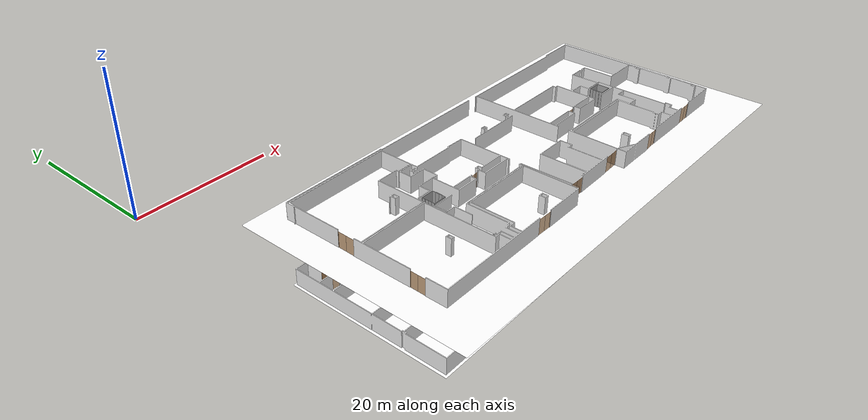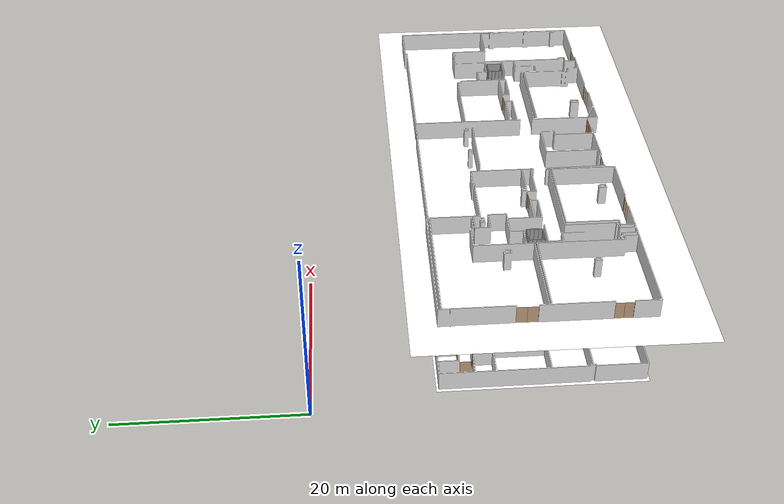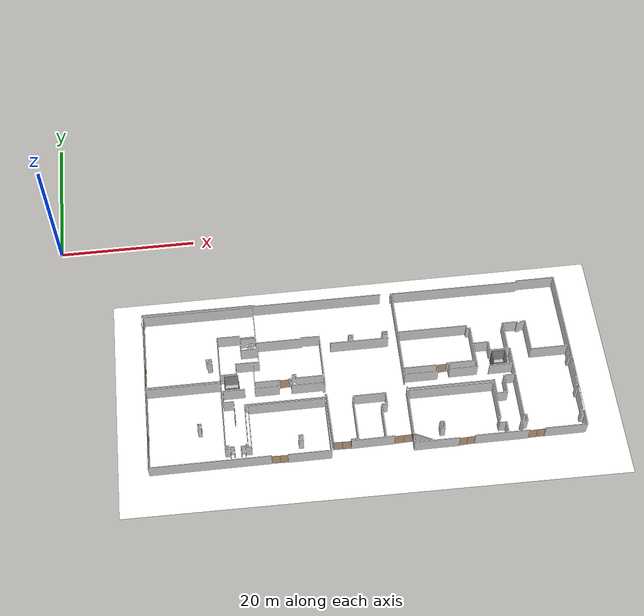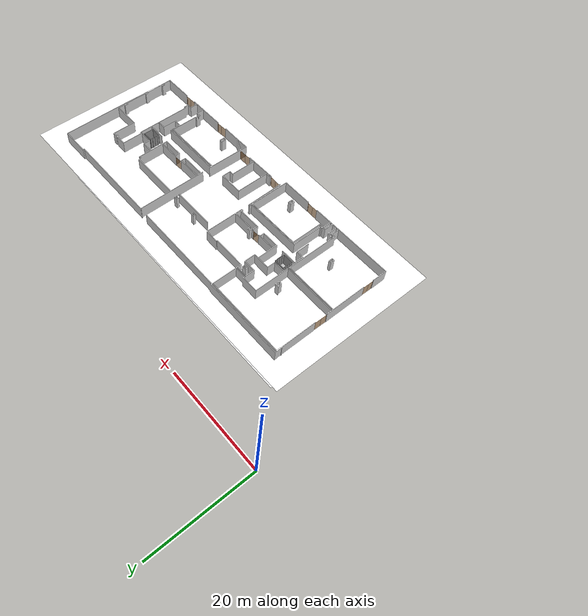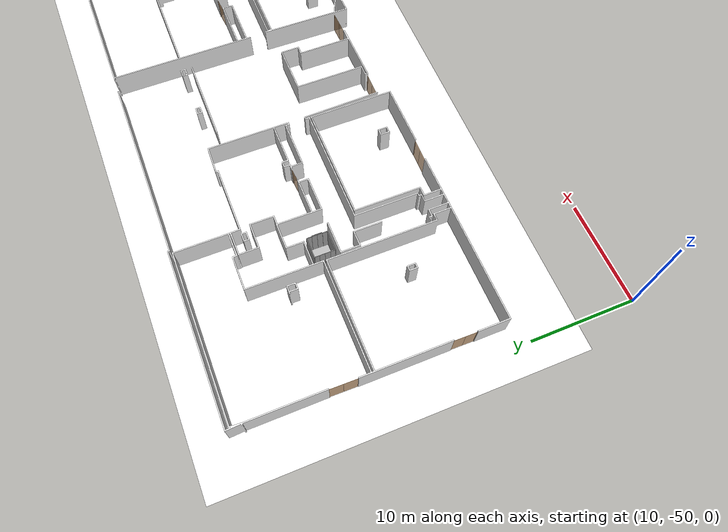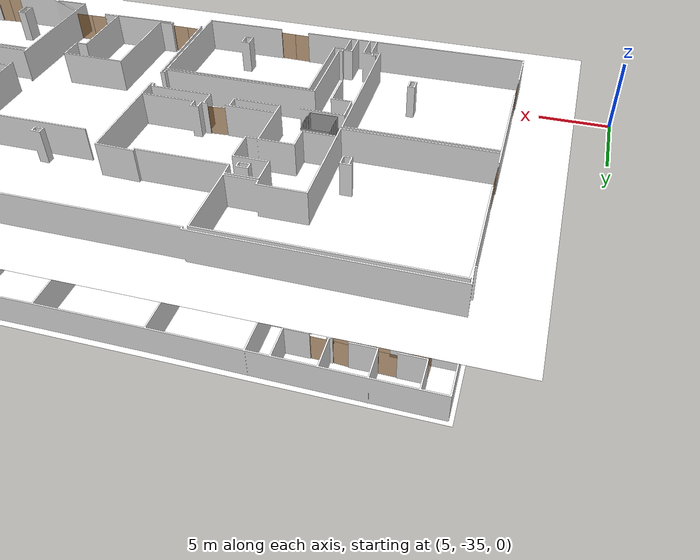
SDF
<sdf version="1.7">
 <world name="sim_world">
  <physics name="10ms" type="ode">
   <max_step_size>0.01</max_step_size>
   <real_time_factor>1.0</real_time_factor>
  </physics>
  <plugin filename="gz-sim-physics-system" name="gz::sim::systems::Physics"/>
  <plugin filename="gz-sim-user-commands-system" name="gz::sim::systems::UserCommands"/>
  <plugin filename="gz-sim-scene-broadcaster-system" name="gz::sim::systems::SceneBroadcaster"/>
  <plugin filename="libdoor.so" name="door"/>
  <plugin filename="liblift.so" name="lift"/>
  <scene><ambient>1 1 1</ambient><background>0.8 0.8 0.8</background><grid>false</grid></scene>
  <light type="directional" name="sun">
   <pose>0 0 10 0 0 0</pose>
   <diffuse>1 1 1 1</diffuse>
   <specular>0.2 0.2 0.2 1</specular>
   <attenuation>
    <range>1000</range>
    <constant>0.09</constant>
    <linear>0.001</linear>
    <quadratic>0.001</quadratic>
   </attenuation>
   <direction>-0.5 0.1 -0.9</direction>
  </light>
  <model name="door1">
   <pose>56.051119570614546 -38.47984300002366 0.0 0 0 -3.084511871183529</pose>
   <link name="right">
    <pose>0.5711190821411659 0 1.11 0 0 0</pose>
    <visual name="right_visual">
     <geometry><box><size>1.1322381642823318 0.03 2.2</size></box></geometry>
     <material>
      <ambient>0.5 0.25 0 0.6</ambient>
      <diffuse>0.5 0.25 0 0.6</diffuse>
      <pbr><metal><metalness>0.0</metalness></metal></pbr>
     </material>
    </visual>
    <collision name="right_collision">
     <geometry><box><size>1.1322381642823318 0.03 2.2</size></box></geometry>
     <surface><contact><collide_bitmask>0x02</collide_bitmask></contact></surface>
    </collision>
    <inertial>
     <mass>50.0</mass>
     <inertia><ixx>20.17041666666667</ixx><iyy>25.508180252739276</iyy><izz>5.345263586072603</izz></inertia>
    </inertial>
   </link>
   <joint name="right_joint" type="revolute">
    <parent>world</parent>
    <child>right</child>
    <axis><xyz>0 0 1</xyz><limit><lower>0</lower><upper>1.57</upper></limit></axis>
    <pose>0.5711190821411659 0 0 0 0 0</pose>
   </joint>
   <link name="left">
    <pose>-0.5711190821411659 0 1.11 0 0 0</pose>
    <visual name="left_visual">
     <geometry><box><size>1.1322381642823318 0.03 2.2</size></box></geometry>
     <material>
      <ambient>0.5 0.25 0 0.6</ambient>
      <diffuse>0.5 0.25 0 0.6</diffuse>
      <pbr><metal><metalness>0.0</metalness></metal></pbr>
     </material>
    </visual>
    <collision name="left_collision">
     <geometry><box><size>1.1322381642823318 0.03 2.2</size></box></geometry>
     <surface><contact><collide_bitmask>0x02</collide_bitmask></contact></surface>
    </collision>
    <inertial>
     <mass>50.0</mass>
     <inertia><ixx>20.17041666666667</ixx><iyy>25.508180252739276</iyy><izz>5.345263586072603</izz></inertia>
    </inertial>
   </link>
   <joint name="left_joint" type="revolute">
    <parent>world</parent>
    <child>left</child>
    <axis><xyz>0 0 1</xyz><limit><lower>-1.57</lower><upper>0</upper></limit></axis>
    <pose>-0.5711190821411659 0 0 0 0 0</pose>
   </joint>
   <plugin name="register_component" filename="libregister_component.so">
    <component name="Door">
     <v_max_door>0.5</v_max_door>
     <a_max_door>0.3</a_max_door>
     <a_nom_door>0.15</a_nom_door>
     <dx_min_door>0.01</dx_min_door>
     <f_max_door>500.0</f_max_door>
     <ros_interface>true</ros_interface>
     <door name="door1" type="DoubleSwingDoor" left_joint_name="left_joint" right_joint_name="right_joint"/>
    </component>
   </plugin>
  </model>
  <model name="door2">
   <pose>65.91755136783867 -38.3843543848864 0.0 0 0 -3.116317636538179</pose>
   <link name="right">
    <pose>0.599948082041474 0 1.11 0 0 0</pose>
    <visual name="right_visual">
     <geometry><box><size>1.189896164082948 0.03 2.2</size></box></geometry>
     <material>
      <ambient>0.5 0.25 0 0.6</ambient>
      <diffuse>0.5 0.25 0 0.6</diffuse>
      <pbr><metal><metalness>0.0</metalness></metal></pbr>
     </material>
    </visual>
    <collision name="right_collision">
     <geometry><box><size>1.189896164082948 0.03 2.2</size></box></geometry>
     <surface><contact><collide_bitmask>0x02</collide_bitmask></contact></surface>
    </collision>
    <inertial>
     <mass>50.0</mass>
     <inertia><ixx>20.17041666666667</ixx><iyy>26.06605367208048</iyy><izz>5.903137005413808</izz></inertia>
    </inertial>
   </link>
   <joint name="right_joint" type="revolute">
    <parent>world</parent>
    <child>right</child>
    <axis><xyz>0 0 1</xyz><limit><lower>0</lower><upper>1.57</upper></limit></axis>
    <pose>0.599948082041474 0 0 0 0 0</pose>
   </joint>
   <link name="left">
    <pose>-0.599948082041474 0 1.11 0 0 0</pose>
    <visual name="left_visual">
     <geometry><box><size>1.189896164082948 0.03 2.2</size></box></geometry>
     <material>
      <ambient>0.5 0.25 0 0.6</ambient>
      <diffuse>0.5 0.25 0 0.6</diffuse>
      <pbr><metal><metalness>0.0</metalness></metal></pbr>
     </material>
    </visual>
    <collision name="left_collision">
     <geometry><box><size>1.189896164082948 0.03 2.2</size></box></geometry>
     <surface><contact><collide_bitmask>0x02</collide_bitmask></contact></surface>
    </collision>
    <inertial>
     <mass>50.0</mass>
     <inertia><ixx>20.17041666666667</ixx><iyy>26.06605367208048</iyy><izz>5.903137005413808</izz></inertia>
    </inertial>
   </link>
   <joint name="left_joint" type="revolute">
    <parent>world</parent>
    <child>left</child>
    <axis><xyz>0 0 1</xyz><limit><lower>-1.57</lower><upper>0</upper></limit></axis>
    <pose>-0.599948082041474 0 0 0 0 0</pose>
   </joint>
   <plugin name="register_component" filename="libregister_component.so">
    <component name="Door">
     <v_max_door>0.5</v_max_door>
     <a_max_door>0.3</a_max_door>
     <a_nom_door>0.15</a_nom_door>
     <dx_min_door>0.01</dx_min_door>
     <f_max_door>500.0</f_max_door>
     <ros_interface>true</ros_interface>
     <door name="door2" type="DoubleSwingDoor" left_joint_name="left_joint" right_joint_name="right_joint"/>
    </component>
   </plugin>
  </model>
  <model name="door3">
   <pose>54.32078594566478 -26.636299151159776 0.0 0 0 0.0715749965452934</pose>
   <link name="right">
    <pose>0 0 1.11 0 0 0</pose>
    <visual name="right_visual">
     <geometry><box><size>1.3878997510727893 0.03 2.2</size></box></geometry>
     <material>
      <ambient>0.5 0.25 0 0.6</ambient>
      <diffuse>0.5 0.25 0 0.6</diffuse>
      <pbr><metal><metalness>0.0</metalness></metal></pbr>
     </material>
    </visual>
    <collision name="right_collision">
     <geometry><box><size>1.3878997510727893 0.03 2.2</size></box></geometry>
     <surface><contact><collide_bitmask>0x02</collide_bitmask></contact></surface>
    </collision>
    <inertial>
     <mass>50.0</mass>
     <inertia><ixx>20.17041666666667</ixx><iyy>28.192773829282967</iyy><izz>8.029857162616294</izz></inertia>
    </inertial>
   </link>
   <joint name="right_joint" type="revolute">
    <parent>world</parent>
    <child>right</child>
    <axis><xyz>0 0 1</xyz><limit><lower>0</lower><upper>1.57</upper></limit></axis>
    <pose>0.6989498755363946 0 0 0 0 0</pose>
   </joint>
   <plugin name="register_component" filename="libregister_component.so">
    <component name="Door">
     <v_max_door>0.5</v_max_door>
     <a_max_door>0.3</a_max_door>
     <a_nom_door>0.15</a_nom_door>
     <dx_min_door>0.01</dx_min_door>
     <f_max_door>500.0</f_max_door>
     <ros_interface>true</ros_interface>
     <door name="door3" type="SwingDoor" left_joint_name="empty_joint" right_joint_name="right_joint"/>
    </component>
   </plugin>
  </model>
  <model name="door4">
   <pose>31.692632350507186 -26.7141489135318 0.0 0 0 0.07624215236291886</pose>
   <link name="right">
    <pose>0 0 1.11 0 0 0</pose>
    <visual name="right_visual">
     <geometry><box><size>1.3456275371306028 0.03 2.2</size></box></geometry>
     <material>
      <ambient>0.5 0.25 0 0.6</ambient>
      <diffuse>0.5 0.25 0 0.6</diffuse>
      <pbr><metal><metalness>0.0</metalness></metal></pbr>
     </material>
    </visual>
    <collision name="right_collision">
     <geometry><box><size>1.3456275371306028 0.03 2.2</size></box></geometry>
     <surface><contact><collide_bitmask>0x02</collide_bitmask></contact></surface>
    </collision>
    <inertial>
     <mass>50.0</mass>
     <inertia><ixx>20.17041666666667</ixx><iyy>27.711306119517385</iyy><izz>7.548389452850715</izz></inertia>
    </inertial>
   </link>
   <joint name="right_joint" type="revolute">
    <parent>world</parent>
    <child>right</child>
    <axis><xyz>0 0 -1</xyz><limit><lower>0</lower><upper>1.57</upper></limit></axis>
    <pose>0.6778137685653014 0 0 0 0 0</pose>
   </joint>
   <plugin name="register_component" filename="libregister_component.so">
    <component name="Door">
     <v_max_door>0.5</v_max_door>
     <a_max_door>0.3</a_max_door>
     <a_nom_door>0.15</a_nom_door>
     <dx_min_door>0.01</dx_min_door>
     <f_max_door>500.0</f_max_door>
     <ros_interface>true</ros_interface>
     <door name="door4" type="SwingDoor" left_joint_name="empty_joint" right_joint_name="right_joint"/>
    </component>
   </plugin>
  </model>
  <model name="door6">
   <pose>11.898422906864024 -34.40214692738752 0.0 0 0 -1.5884948974328337</pose>
   <link name="right">
    <pose>0.5618003268061672 0 1.11 0 0 0</pose>
    <visual name="right_visual">
     <geometry><box><size>1.1136006536123344 0.03 2.2</size></box></geometry>
     <material>
      <ambient>0.5 0.25 0 0.6</ambient>
      <diffuse>0.5 0.25 0 0.6</diffuse>
      <pbr><metal><metalness>0.0</metalness></metal></pbr>
     </material>
    </visual>
    <collision name="right_collision">
     <geometry><box><size>1.1136006536123344 0.03 2.2</size></box></geometry>
     <surface><contact><collide_bitmask>0x02</collide_bitmask></contact></surface>
    </collision>
    <inertial>
     <mass>50.0</mass>
     <inertia><ixx>20.17041666666667</ixx><iyy>25.333776732190913</iyy><izz>5.170860065524243</izz></inertia>
    </inertial>
   </link>
   <joint name="right_joint" type="revolute">
    <parent>world</parent>
    <child>right</child>
    <axis><xyz>0 0 -1</xyz><limit><lower>0</lower><upper>1.57</upper></limit></axis>
    <pose>0.5618003268061672 0 0 0 0 0</pose>
   </joint>
   <link name="left">
    <pose>-0.5618003268061672 0 1.11 0 0 0</pose>
    <visual name="left_visual">
     <geometry><box><size>1.1136006536123344 0.03 2.2</size></box></geometry>
     <material>
      <ambient>0.5 0.25 0 0.6</ambient>
      <diffuse>0.5 0.25 0 0.6</diffuse>
      <pbr><metal><metalness>0.0</metalness></metal></pbr>
     </material>
    </visual>
    <collision name="left_collision">
     <geometry><box><size>1.1136006536123344 0.03 2.2</size></box></geometry>
     <surface><contact><collide_bitmask>0x02</collide_bitmask></contact></surface>
    </collision>
    <inertial>
     <mass>50.0</mass>
     <inertia><ixx>20.17041666666667</ixx><iyy>25.333776732190913</iyy><izz>5.170860065524243</izz></inertia>
    </inertial>
   </link>
   <joint name="left_joint" type="revolute">
    <parent>world</parent>
    <child>left</child>
    <axis><xyz>0 0 -1</xyz><limit><lower>-1.57</lower><upper>0</upper></limit></axis>
    <pose>-0.5618003268061672 0 0 0 0 0</pose>
   </joint>
   <plugin name="register_component" filename="libregister_component.so">
    <component name="Door">
     <v_max_door>0.5</v_max_door>
     <a_max_door>0.3</a_max_door>
     <a_nom_door>0.15</a_nom_door>
     <dx_min_door>0.01</dx_min_door>
     <f_max_door>500.0</f_max_door>
     <ros_interface>true</ros_interface>
     <door name="door6" type="DoubleSwingDoor" left_joint_name="left_joint" right_joint_name="right_joint"/>
    </component>
   </plugin>
  </model>
  <model name="door7">
   <pose>29.91260965171542 -38.467831556049475 0.0 0 0 3.1163443786232454</pose>
   <link name="right">
    <pose>0.5886419665648434 0 1.11 0 0 0</pose>
    <visual name="right_visual">
     <geometry><box><size>1.1672839331296867 0.03 2.2</size></box></geometry>
     <material>
      <ambient>0.5 0.25 0 0.6</ambient>
      <diffuse>0.5 0.25 0 0.6</diffuse>
      <pbr><metal><metalness>0.0</metalness></metal></pbr>
     </material>
    </visual>
    <collision name="right_collision">
     <geometry><box><size>1.1672839331296867 0.03 2.2</size></box></geometry>
     <surface><contact><collide_bitmask>0x02</collide_bitmask></contact></surface>
    </collision>
    <inertial>
     <mass>50.0</mass>
     <inertia><ixx>20.17041666666667</ixx><iyy>25.8439657522613</iyy><izz>5.681049085594629</izz></inertia>
    </inertial>
   </link>
   <joint name="right_joint" type="revolute">
    <parent>world</parent>
    <child>right</child>
    <axis><xyz>0 0 1</xyz><limit><lower>0</lower><upper>1.57</upper></limit></axis>
    <pose>0.5886419665648434 0 0 0 0 0</pose>
   </joint>
   <link name="left">
    <pose>-0.5886419665648434 0 1.11 0 0 0</pose>
    <visual name="left_visual">
     <geometry><box><size>1.1672839331296867 0.03 2.2</size></box></geometry>
     <material>
      <ambient>0.5 0.25 0 0.6</ambient>
      <diffuse>0.5 0.25 0 0.6</diffuse>
      <pbr><metal><metalness>0.0</metalness></metal></pbr>
     </material>
    </visual>
    <collision name="left_collision">
     <geometry><box><size>1.1672839331296867 0.03 2.2</size></box></geometry>
     <surface><contact><collide_bitmask>0x02</collide_bitmask></contact></surface>
    </collision>
    <inertial>
     <mass>50.0</mass>
     <inertia><ixx>20.17041666666667</ixx><iyy>25.8439657522613</iyy><izz>5.681049085594629</izz></inertia>
    </inertial>
   </link>
   <joint name="left_joint" type="revolute">
    <parent>world</parent>
    <child>left</child>
    <axis><xyz>0 0 1</xyz><limit><lower>-1.57</lower><upper>0</upper></limit></axis>
    <pose>-0.5886419665648434 0 0 0 0 0</pose>
   </joint>
   <plugin name="register_component" filename="libregister_component.so">
    <component name="Door">
     <v_max_door>0.5</v_max_door>
     <a_max_door>0.3</a_max_door>
     <a_nom_door>0.15</a_nom_door>
     <dx_min_door>0.01</dx_min_door>
     <f_max_door>500.0</f_max_door>
     <ros_interface>true</ros_interface>
     <door name="door7" type="DoubleSwingDoor" left_joint_name="left_joint" right_joint_name="right_joint"/>
    </component>
   </plugin>
  </model>
  <model name="door8">
   <pose>11.94001371385336 -23.66581940273805 0.0 0 0 -1.5875025411483974</pose>
   <link name="right">
    <pose>0.6496603259492142 0 1.11 0 0 0</pose>
    <visual name="right_visual">
     <geometry><box><size>1.2893206518984284 0.03 2.2</size></box></geometry>
     <material>
      <ambient>0.5 0.25 0 0.6</ambient>
      <diffuse>0.5 0.25 0 0.6</diffuse>
      <pbr><metal><metalness>0.0</metalness></metal></pbr>
     </material>
    </visual>
    <collision name="right_collision">
     <geometry><box><size>1.2893206518984284 0.03 2.2</size></box></geometry>
     <surface><contact><collide_bitmask>0x02</collide_bitmask></contact></surface>
    </collision>
    <inertial>
     <mass>50.0</mass>
     <inertia><ixx>20.17041666666667</ixx><iyy>27.093115597549126</iyy><izz>6.930198930882452</izz></inertia>
    </inertial>
   </link>
   <joint name="right_joint" type="revolute">
    <parent>world</parent>
    <child>right</child>
    <axis><xyz>0 0 -1</xyz><limit><lower>0</lower><upper>1.57</upper></limit></axis>
    <pose>0.6496603259492142 0 0 0 0 0</pose>
   </joint>
   <link name="left">
    <pose>-0.6496603259492142 0 1.11 0 0 0</pose>
    <visual name="left_visual">
     <geometry><box><size>1.2893206518984284 0.03 2.2</size></box></geometry>
     <material>
      <ambient>0.5 0.25 0 0.6</ambient>
      <diffuse>0.5 0.25 0 0.6</diffuse>
      <pbr><metal><metalness>0.0</metalness></metal></pbr>
     </material>
    </visual>
    <collision name="left_collision">
     <geometry><box><size>1.2893206518984284 0.03 2.2</size></box></geometry>
     <surface><contact><collide_bitmask>0x02</collide_bitmask></contact></surface>
    </collision>
    <inertial>
     <mass>50.0</mass>
     <inertia><ixx>20.17041666666667</ixx><iyy>27.093115597549126</iyy><izz>6.930198930882452</izz></inertia>
    </inertial>
   </link>
   <joint name="left_joint" type="revolute">
    <parent>world</parent>
    <child>left</child>
    <axis><xyz>0 0 -1</xyz><limit><lower>-1.57</lower><upper>0</upper></limit></axis>
    <pose>-0.6496603259492142 0 0 0 0 0</pose>
   </joint>
   <plugin name="register_component" filename="libregister_component.so">
    <component name="Door">
     <v_max_door>0.5</v_max_door>
     <a_max_door>0.3</a_max_door>
     <a_nom_door>0.15</a_nom_door>
     <dx_min_door>0.01</dx_min_door>
     <f_max_door>500.0</f_max_door>
     <ros_interface>true</ros_interface>
     <door name="door8" type="DoubleSwingDoor" left_joint_name="left_joint" right_joint_name="right_joint"/>
    </component>
   </plugin>
  </model>
  <model name="door9">
   <pose>38.739235807344016 -37.32229919844893 0.0 0 0 3.1234123269400906</pose>
   <link name="right">
    <pose>0.6301552102107287 0 1.11 0 0 0</pose>
    <visual name="right_visual">
     <geometry><box><size>1.2503104204214575 0.03 2.2</size></box></geometry>
     <material>
      <ambient>0.5 0.25 0 0.6</ambient>
      <diffuse>0.5 0.25 0 0.6</diffuse>
      <pbr><metal><metalness>0.0</metalness></metal></pbr>
     </material>
    </visual>
    <collision name="right_collision">
     <geometry><box><size>1.2503104204214575 0.03 2.2</size></box></geometry>
     <surface><contact><collide_bitmask>0x02</collide_bitmask></contact></surface>
    </collision>
    <inertial>
     <mass>50.0</mass>
     <inertia><ixx>20.17041666666667</ixx><iyy>26.68031728089368</iyy><izz>6.5174006142270065</izz></inertia>
    </inertial>
   </link>
   <joint name="right_joint" type="revolute">
    <parent>world</parent>
    <child>right</child>
    <axis><xyz>0 0 -1</xyz><limit><lower>0</lower><upper>1.57</upper></limit></axis>
    <pose>0.6301552102107287 0 0 0 0 0</pose>
   </joint>
   <link name="left">
    <pose>-0.6301552102107287 0 1.11 0 0 0</pose>
    <visual name="left_visual">
     <geometry><box><size>1.2503104204214575 0.03 2.2</size></box></geometry>
     <material>
      <ambient>0.5 0.25 0 0.6</ambient>
      <diffuse>0.5 0.25 0 0.6</diffuse>
      <pbr><metal><metalness>0.0</metalness></metal></pbr>
     </material>
    </visual>
    <collision name="left_collision">
     <geometry><box><size>1.2503104204214575 0.03 2.2</size></box></geometry>
     <surface><contact><collide_bitmask>0x02</collide_bitmask></contact></surface>
    </collision>
    <inertial>
     <mass>50.0</mass>
     <inertia><ixx>20.17041666666667</ixx><iyy>26.68031728089368</iyy><izz>6.5174006142270065</izz></inertia>
    </inertial>
   </link>
   <joint name="left_joint" type="revolute">
    <parent>world</parent>
    <child>left</child>
    <axis><xyz>0 0 -1</xyz><limit><lower>-1.57</lower><upper>0</upper></limit></axis>
    <pose>-0.6301552102107287 0 0 0 0 0</pose>
   </joint>
   <plugin name="register_component" filename="libregister_component.so">
    <component name="Door">
     <v_max_door>0.5</v_max_door>
     <a_max_door>0.3</a_max_door>
     <a_nom_door>0.15</a_nom_door>
     <dx_min_door>0.01</dx_min_door>
     <f_max_door>500.0</f_max_door>
     <ros_interface>true</ros_interface>
     <door name="door9" type="DoubleSwingDoor" left_joint_name="left_joint" right_joint_name="right_joint"/>
    </component>
   </plugin>
  </model>
  <model name="door10">
   <pose>47.33296290166223 -37.23722601849007 0.0 0 0 -3.113147754585356</pose>
   <link name="right">
    <pose>0.673811932769585 0 1.11 0 0 0</pose>
    <visual name="right_visual">
     <geometry><box><size>1.33762386553917 0.03 2.2</size></box></geometry>
     <material>
      <ambient>0.5 0.25 0 0.6</ambient>
      <diffuse>0.5 0.25 0 0.6</diffuse>
      <pbr><metal><metalness>0.0</metalness></metal></pbr>
     </material>
    </visual>
    <collision name="right_collision">
     <geometry><box><size>1.33762386553917 0.03 2.2</size></box></geometry>
     <surface><contact><collide_bitmask>0x02</collide_bitmask></contact></surface>
    </collision>
    <inertial>
     <mass>50.0</mass>
     <inertia><ixx>20.17041666666667</ixx><iyy>27.62182335691647</iyy><izz>7.458906690249797</izz></inertia>
    </inertial>
   </link>
   <joint name="right_joint" type="revolute">
    <parent>world</parent>
    <child>right</child>
    <axis><xyz>0 0 -1</xyz><limit><lower>0</lower><upper>1.57</upper></limit></axis>
    <pose>0.673811932769585 0 0 0 0 0</pose>
   </joint>
   <link name="left">
    <pose>-0.673811932769585 0 1.11 0 0 0</pose>
    <visual name="left_visual">
     <geometry><box><size>1.33762386553917 0.03 2.2</size></box></geometry>
     <material>
      <ambient>0.5 0.25 0 0.6</ambient>
      <diffuse>0.5 0.25 0 0.6</diffuse>
      <pbr><metal><metalness>0.0</metalness></metal></pbr>
     </material>
    </visual>
    <collision name="left_collision">
     <geometry><box><size>1.33762386553917 0.03 2.2</size></box></geometry>
     <surface><contact><collide_bitmask>0x02</collide_bitmask></contact></surface>
    </collision>
    <inertial>
     <mass>50.0</mass>
     <inertia><ixx>20.17041666666667</ixx><iyy>27.62182335691647</iyy><izz>7.458906690249797</izz></inertia>
    </inertial>
   </link>
   <joint name="left_joint" type="revolute">
    <parent>world</parent>
    <child>left</child>
    <axis><xyz>0 0 -1</xyz><limit><lower>-1.57</lower><upper>0</upper></limit></axis>
    <pose>-0.673811932769585 0 0 0 0 0</pose>
   </joint>
   <plugin name="register_component" filename="libregister_component.so">
    <component name="Door">
     <v_max_door>0.5</v_max_door>
     <a_max_door>0.3</a_max_door>
     <a_nom_door>0.15</a_nom_door>
     <dx_min_door>0.01</dx_min_door>
     <f_max_door>500.0</f_max_door>
     <ros_interface>true</ros_interface>
     <door name="door10" type="DoubleSwingDoor" left_joint_name="left_joint" right_joint_name="right_joint"/>
    </component>
   </plugin>
  </model>
  <include><name>industrial_L1</name><uri>model://industrial_L1</uri></include>
  <model name="door11">
   <pose>22.026146063012423 -19.219296318400083 -10.0 0 0 3.135121069938691</pose>
   <link name="right">
    <pose>0 0 1.11 0 0 0</pose>
    <visual name="right_visual">
     <geometry><box><size>1.400921036440383 0.03 2.2</size></box></geometry>
     <material>
      <ambient>0.5 0.25 0 0.6</ambient>
      <diffuse>0.5 0.25 0 0.6</diffuse>
      <pbr><metal><metalness>0.0</metalness></metal></pbr>
     </material>
    </visual>
    <collision name="right_collision">
     <geometry><box><size>1.400921036440383 0.03 2.2</size></box></geometry>
     <surface><contact><collide_bitmask>0x02</collide_bitmask></contact></surface>
    </collision>
    <inertial>
     <mass>50.0</mass>
     <inertia><ixx>20.17041666666667</ixx><iyy>28.344082293088327</iyy><izz>8.181165626421654</izz></inertia>
    </inertial>
   </link>
   <joint name="right_joint" type="revolute">
    <parent>world</parent>
    <child>right</child>
    <axis><xyz>0 0 1</xyz><limit><lower>0</lower><upper>1.57</upper></limit></axis>
    <pose>0.7054605182201915 0 0 0 0 0</pose>
   </joint>
   <plugin name="register_component" filename="libregister_component.so">
    <component name="Door">
     <v_max_door>0.5</v_max_door>
     <a_max_door>0.3</a_max_door>
     <a_nom_door>0.15</a_nom_door>
     <dx_min_door>0.01</dx_min_door>
     <f_max_door>500.0</f_max_door>
     <ros_interface>true</ros_interface>
     <door name="door11" type="SwingDoor" left_joint_name="empty_joint" right_joint_name="right_joint"/>
    </component>
   </plugin>
  </model>
  <model name="door12">
   <pose>22.91654270555554 -18.15974682081672 -10.0 0 0 1.6228104030850234</pose>
   <link name="right">
    <pose>0 0 1.11 0 0 0</pose>
    <visual name="right_visual">
     <geometry><box><size>1.2975872639959458 0.03 2.2</size></box></geometry>
     <material>
      <ambient>0.5 0.25 0 0.6</ambient>
      <diffuse>0.5 0.25 0 0.6</diffuse>
      <pbr><metal><metalness>0.0</metalness></metal></pbr>
     </material>
    </visual>
    <collision name="right_collision">
     <geometry><box><size>1.2975872639959458 0.03 2.2</size></box></geometry>
     <surface><contact><collide_bitmask>0x02</collide_bitmask></contact></surface>
    </collision>
    <inertial>
     <mass>50.0</mass>
     <inertia><ixx>20.17041666666667</ixx><iyy>27.18221961535202</iyy><izz>7.019302948685351</izz></inertia>
    </inertial>
   </link>
   <joint name="right_joint" type="revolute">
    <parent>world</parent>
    <child>right</child>
    <axis><xyz>0 0 -1</xyz><limit><lower>0</lower><upper>1.57</upper></limit></axis>
    <pose>0.6537936319979729 0 0 0 0 0</pose>
   </joint>
   <plugin name="register_component" filename="libregister_component.so">
    <component name="Door">
     <v_max_door>0.5</v_max_door>
     <a_max_door>0.3</a_max_door>
     <a_nom_door>0.15</a_nom_door>
     <dx_min_door>0.01</dx_min_door>
     <f_max_door>500.0</f_max_door>
     <ros_interface>true</ros_interface>
     <door name="door12" type="SwingDoor" left_joint_name="empty_joint" right_joint_name="right_joint"/>
    </component>
   </plugin>
  </model>
  <model name="door13">
   <pose>21.503290849951316 -16.702407413810654 -10.0 0 0 -0.008515079477213769</pose>
   <link name="right">
    <pose>0 0 1.11 0 0 0</pose>
    <visual name="right_visual">
     <geometry><box><size>1.2621048951653506 0.03 2.2</size></box></geometry>
     <material>
      <ambient>0.5 0.25 0 0.6</ambient>
      <diffuse>0.5 0.25 0 0.6</diffuse>
      <pbr><metal><metalness>0.0</metalness></metal></pbr>
     </material>
    </visual>
    <collision name="right_collision">
     <geometry><box><size>1.2621048951653506 0.03 2.2</size></box></geometry>
     <surface><contact><collide_bitmask>0x02</collide_bitmask></contact></surface>
    </collision>
    <inertial>
     <mass>50.0</mass>
     <inertia><ixx>20.17041666666667</ixx><iyy>26.80378652666809</iyy><izz>6.64086986000142</izz></inertia>
    </inertial>
   </link>
   <joint name="right_joint" type="revolute">
    <parent>world</parent>
    <child>right</child>
    <axis><xyz>0 0 1</xyz><limit><lower>0</lower><upper>1.57</upper></limit></axis>
    <pose>0.6360524475826753 0 0 0 0 0</pose>
   </joint>
   <plugin name="register_component" filename="libregister_component.so">
    <component name="Door">
     <v_max_door>0.5</v_max_door>
     <a_max_door>0.3</a_max_door>
     <a_nom_door>0.15</a_nom_door>
     <dx_min_door>0.01</dx_min_door>
     <f_max_door>500.0</f_max_door>
     <ros_interface>true</ros_interface>
     <door name="door13" type="SwingDoor" left_joint_name="empty_joint" right_joint_name="right_joint"/>
    </component>
   </plugin>
  </model>
  <model name="door14">
   <pose>19.955417811509754 -16.680424650825586 -10.0 0 0 -0.06561283704825525</pose>
   <link name="right">
    <pose>0 0 1.11 0 0 0</pose>
    <visual name="right_visual">
     <geometry><box><size>1.18585136485352 0.03 2.2</size></box></geometry>
     <material>
      <ambient>0.5 0.25 0 0.6</ambient>
      <diffuse>0.5 0.25 0 0.6</diffuse>
      <pbr><metal><metalness>0.0</metalness></metal></pbr>
     </material>
    </visual>
    <collision name="right_collision">
     <geometry><box><size>1.18585136485352 0.03 2.2</size></box></geometry>
     <surface><contact><collide_bitmask>0x02</collide_bitmask></contact></surface>
    </collision>
    <inertial>
     <mass>50.0</mass>
     <inertia><ixx>20.17041666666667</ixx><iyy>26.026014414687324</iyy><izz>5.863097748020651</izz></inertia>
    </inertial>
   </link>
   <joint name="right_joint" type="revolute">
    <parent>world</parent>
    <child>right</child>
    <axis><xyz>0 0 -1</xyz><limit><lower>0</lower><upper>1.57</upper></limit></axis>
    <pose>0.59792568242676 0 0 0 0 0</pose>
   </joint>
   <plugin name="register_component" filename="libregister_component.so">
    <component name="Door">
     <v_max_door>0.5</v_max_door>
     <a_max_door>0.3</a_max_door>
     <a_nom_door>0.15</a_nom_door>
     <dx_min_door>0.01</dx_min_door>
     <f_max_door>500.0</f_max_door>
     <ros_interface>true</ros_interface>
     <door name="door14" type="SwingDoor" left_joint_name="empty_joint" right_joint_name="right_joint"/>
    </component>
   </plugin>
  </model>
  <model name="door15">
   <pose>16.75273322700722 -16.636459157596292 -10.0 0 0 -0.007930178567556635</pose>
   <link name="right">
    <pose>0 0 1.11 0 0 0</pose>
    <visual name="right_visual">
     <geometry><box><size>1.3521588121064176 0.03 2.2</size></box></geometry>
     <material>
      <ambient>0.5 0.25 0 0.6</ambient>
      <diffuse>0.5 0.25 0 0.6</diffuse>
      <pbr><metal><metalness>0.0</metalness></metal></pbr>
     </material>
    </visual>
    <collision name="right_collision">
     <geometry><box><size>1.3521588121064176 0.03 2.2</size></box></geometry>
     <surface><contact><collide_bitmask>0x02</collide_bitmask></contact></surface>
    </collision>
    <inertial>
     <mass>50.0</mass>
     <inertia><ixx>20.17041666666667</ixx><iyy>27.784722721487668</iyy><izz>7.621806054820994</izz></inertia>
    </inertial>
   </link>
   <joint name="right_joint" type="revolute">
    <parent>world</parent>
    <child>right</child>
    <axis><xyz>0 0 -1</xyz><limit><lower>0</lower><upper>1.57</upper></limit></axis>
    <pose>0.6810794060532088 0 0 0 0 0</pose>
   </joint>
   <plugin name="register_component" filename="libregister_component.so">
    <component name="Door">
     <v_max_door>0.5</v_max_door>
     <a_max_door>0.3</a_max_door>
     <a_nom_door>0.15</a_nom_door>
     <dx_min_door>0.01</dx_min_door>
     <f_max_door>500.0</f_max_door>
     <ros_interface>true</ros_interface>
     <door name="door15" type="SwingDoor" left_joint_name="empty_joint" right_joint_name="right_joint"/>
    </component>
   </plugin>
  </model>
  <model name="door16">
   <pose>14.103867444886037 -17.372549540097616 -10.0 0 0 1.5433859809884722</pose>
   <link name="right">
    <pose>0 0 1.11 0 0 0</pose>
    <visual name="right_visual">
     <geometry><box><size>1.472246684621956 0.03 2.2</size></box></geometry>
     <material>
      <ambient>0.5 0.25 0 0.6</ambient>
      <diffuse>0.5 0.25 0 0.6</diffuse>
      <pbr><metal><metalness>0.0</metalness></metal></pbr>
     </material>
    </visual>
    <collision name="right_collision">
     <geometry><box><size>1.472246684621956 0.03 2.2</size></box></geometry>
     <surface><contact><collide_bitmask>0x02</collide_bitmask></contact></surface>
    </collision>
    <inertial>
     <mass>50.0</mass>
     <inertia><ixx>20.17041666666667</ixx><iyy>29.19795958491809</iyy><izz>9.035042918251422</izz></inertia>
    </inertial>
   </link>
   <joint name="right_joint" type="revolute">
    <parent>world</parent>
    <child>right</child>
    <axis><xyz>0 0 1</xyz><limit><lower>0</lower><upper>1.57</upper></limit></axis>
    <pose>0.741123342310978 0 0 0 0 0</pose>
   </joint>
   <plugin name="register_component" filename="libregister_component.so">
    <component name="Door">
     <v_max_door>0.5</v_max_door>
     <a_max_door>0.3</a_max_door>
     <a_nom_door>0.15</a_nom_door>
     <dx_min_door>0.01</dx_min_door>
     <f_max_door>500.0</f_max_door>
     <ros_interface>true</ros_interface>
     <door name="door16" type="SwingDoor" left_joint_name="empty_joint" right_joint_name="right_joint"/>
    </component>
   </plugin>
  </model>
  <model name="door17">
   <pose>14.94088052865908 -18.280598823191003 -10.0 0 0 3.0943538494370033</pose>
   <link name="right">
    <pose>0 0 1.11 0 0 0</pose>
    <visual name="right_visual">
     <geometry><box><size>1.1733365822123862 0.03 2.2</size></box></geometry>
     <material>
      <ambient>0.5 0.25 0 0.6</ambient>
      <diffuse>0.5 0.25 0 0.6</diffuse>
      <pbr><metal><metalness>0.0</metalness></metal></pbr>
     </material>
    </visual>
    <collision name="right_collision">
     <geometry><box><size>1.1733365822123862 0.03 2.2</size></box></geometry>
     <surface><contact><collide_bitmask>0x02</collide_bitmask></contact></surface>
    </collision>
    <inertial>
     <mass>50.0</mass>
     <inertia><ixx>20.17041666666667</ixx><iyy>25.902994729824353</iyy><izz>5.740078063157682</izz></inertia>
    </inertial>
   </link>
   <joint name="right_joint" type="revolute">
    <parent>world</parent>
    <child>right</child>
    <axis><xyz>0 0 1</xyz><limit><lower>0</lower><upper>1.57</upper></limit></axis>
    <pose>0.5916682911061931 0 0 0 0 0</pose>
   </joint>
   <plugin name="register_component" filename="libregister_component.so">
    <component name="Door">
     <v_max_door>0.5</v_max_door>
     <a_max_door>0.3</a_max_door>
     <a_nom_door>0.15</a_nom_door>
     <dx_min_door>0.01</dx_min_door>
     <f_max_door>500.0</f_max_door>
     <ros_interface>true</ros_interface>
     <door name="door17" type="SwingDoor" left_joint_name="empty_joint" right_joint_name="right_joint"/>
    </component>
   </plugin>
  </model>
  <model name="door18">
   <pose>17.569435664863242 -18.324754895509002 -10.0 0 0 -0.025097312929579885</pose>
   <link name="right">
    <pose>0 0 1.11 0 0 0</pose>
    <visual name="right_visual">
     <geometry><box><size>1.3187793357036819 0.03 2.2</size></box></geometry>
     <material>
      <ambient>0.5 0.25 0 0.6</ambient>
      <diffuse>0.5 0.25 0 0.6</diffuse>
      <pbr><metal><metalness>0.0</metalness></metal></pbr>
     </material>
    </visual>
    <collision name="right_collision">
     <geometry><box><size>1.3187793357036819 0.03 2.2</size></box></geometry>
     <surface><contact><collide_bitmask>0x02</collide_bitmask></contact></surface>
    </collision>
    <inertial>
     <mass>50.0</mass>
     <inertia><ixx>20.17041666666667</ixx><iyy>27.413245567829357</iyy><izz>7.2503289011626855</izz></inertia>
    </inertial>
   </link>
   <joint name="right_joint" type="revolute">
    <parent>world</parent>
    <child>right</child>
    <axis><xyz>0 0 -1</xyz><limit><lower>0</lower><upper>1.57</upper></limit></axis>
    <pose>0.664389667851841 0 0 0 0 0</pose>
   </joint>
   <plugin name="register_component" filename="libregister_component.so">
    <component name="Door">
     <v_max_door>0.5</v_max_door>
     <a_max_door>0.3</a_max_door>
     <a_nom_door>0.15</a_nom_door>
     <dx_min_door>0.01</dx_min_door>
     <f_max_door>500.0</f_max_door>
     <ros_interface>true</ros_interface>
     <door name="door18" type="SwingDoor" left_joint_name="empty_joint" right_joint_name="right_joint"/>
    </component>
   </plugin>
  </model>
  <model name="door19">
   <pose>20.37946613005124 -18.33755886100709 -10.0 0 0 -3.136219686990642</pose>
   <link name="right">
    <pose>0 0 1.11 0 0 0</pose>
    <visual name="right_visual">
     <geometry><box><size>1.2422816077458356 0.03 2.2</size></box></geometry>
     <material>
      <ambient>0.5 0.25 0 0.6</ambient>
      <diffuse>0.5 0.25 0 0.6</diffuse>
      <pbr><metal><metalness>0.0</metalness></metal></pbr>
     </material>
    </visual>
    <collision name="right_collision">
     <geometry><box><size>1.2422816077458356 0.03 2.2</size></box></geometry>
     <surface><contact><collide_bitmask>0x02</collide_bitmask></contact></surface>
    </collision>
    <inertial>
     <mass>50.0</mass>
     <inertia><ixx>20.17041666666667</ixx><iyy>26.596931637264916</iyy><izz>6.434014970598243</izz></inertia>
    </inertial>
   </link>
   <joint name="right_joint" type="revolute">
    <parent>world</parent>
    <child>right</child>
    <axis><xyz>0 0 1</xyz><limit><lower>0</lower><upper>1.57</upper></limit></axis>
    <pose>0.6261408038729178 0 0 0 0 0</pose>
   </joint>
   <plugin name="register_component" filename="libregister_component.so">
    <component name="Door">
     <v_max_door>0.5</v_max_door>
     <a_max_door>0.3</a_max_door>
     <a_nom_door>0.15</a_nom_door>
     <dx_min_door>0.01</dx_min_door>
     <f_max_door>500.0</f_max_door>
     <ros_interface>true</ros_interface>
     <door name="door19" type="SwingDoor" left_joint_name="empty_joint" right_joint_name="right_joint"/>
    </component>
   </plugin>
  </model>
  <include><name>industrial_S1</name><uri>model://industrial_S1</uri><pose>0 0 -10.0 0 0 0</pose></include>
  <model name="ShaftDoor_lift1_L1_doorL1">
   <pose>25.16746624736955 -26.387345423592567 0.0 0 0 -1.57</pose>
   <link name="right_door">
    <pose>0.25 0 1.25 0 0 0</pose>
    <visual name="right_door_visual">
     <geometry><box><size>0.5 0.03 2.5</size></box></geometry>
     <material>
      <ambient>0.5 0.5 0.5 1</ambient>
      <diffuse>0.7 0.7 0.7 1</diffuse>
      <specular>0.6 0.6 0.6 1</specular>
      <emissive>0.1 0.1 0.1 1</emissive>
     </material>
    </visual>
    <collision name="right_door_collision">
     <geometry><box><size>0.5 0.03 2.5</size></box></geometry>
     <surface><contact><collide_bitmask>0x02</collide_bitmask></contact></surface>
    </collision>
   </link>
   <link name="left_door">
    <pose>-0.25 0 1.25 0 0 0</pose>
    <visual name="left_door_visual">
     <geometry><box><size>0.5 0.03 2.5</size></box></geometry>
     <material>
      <ambient>0.5 0.5 0.5 1</ambient>
      <diffuse>0.7 0.7 0.7 1</diffuse>
      <specular>0.6 0.6 0.6 1</specular>
      <emissive>0.1 0.1 0.1 1</emissive>
     </material>
    </visual>
    <collision name="left_door_collision">
     <geometry><box><size>0.5 0.03 2.5</size></box></geometry>
     <surface><contact><collide_bitmask>0x02</collide_bitmask></contact></surface>
    </collision>
   </link>
   <joint name="right_joint" type="prismatic">
    <parent>world</parent>
    <child>right_door</child>
    <axis><xyz>1 0 0</xyz><limit><lower>0</lower><upper>0.5</upper></limit></axis>
   </joint>
   <joint name="left_joint" type="prismatic">
    <parent>world</parent>
    <child>left_door</child>
    <axis><xyz>1 0 0</xyz><limit><lower>-0.5</lower><upper>0</upper></limit></axis>
   </joint>
   <link name="ramp">
    <pose>0 0 -0.025 0 0 0</pose>
    <visual name="ramp_visual">
     <geometry><box><size>1.0 0.1 0.05</size></box></geometry>
     <material>
      <ambient>0.5 0.5 0.5 1</ambient>
      <diffuse>0.7 0.7 0.7 1</diffuse>
      <specular>0.6 0.6 0.6 1</specular>
      <emissive>0.1 0.1 0.1 1</emissive>
     </material>
    </visual>
    <collision name="ramp_collision">
     <geometry><box><size>1.0 0.1 0.05</size></box></geometry>
     <surface><contact><collide_bitmask>0x02</collide_bitmask></contact></surface>
    </collision>
   </link>
   <joint name="ramp_joint" type="fixed"><parent>world</parent><child>ramp</child></joint>
   <plugin name="register_component" filename="libregister_component.so">
    <component name="Door">
     <v_max_door>0.3</v_max_door>
     <a_max_door>0.2</a_max_door>
     <a_nom_door>0.1</a_nom_door>
     <dx_min_door>0.0001</dx_min_door>
     <f_max_door>35.0</f_max_door>
     <door left_joint_name="left_joint" name="ShaftDoor_lift1_L1_doorL1" right_joint_name="right_joint" type="DoubleSlidingDoor"/>
    </component>
   </plugin>
  </model>
  <model name="ShaftDoor_lift1_S1_doorS1">
   <pose>23.06746624736955 -26.387345423592567 -10.0 0 0 -1.57</pose>
   <link name="right_door">
    <pose>0.25 0 1.25 0 0 0</pose>
    <visual name="right_door_visual">
     <geometry><box><size>0.5 0.03 2.5</size></box></geometry>
     <material>
      <ambient>0.5 0.5 0.5 1</ambient>
      <diffuse>0.7 0.7 0.7 1</diffuse>
      <specular>0.6 0.6 0.6 1</specular>
      <emissive>0.1 0.1 0.1 1</emissive>
     </material>
    </visual>
    <collision name="right_door_collision">
     <geometry><box><size>0.5 0.03 2.5</size></box></geometry>
     <surface><contact><collide_bitmask>0x02</collide_bitmask></contact></surface>
    </collision>
   </link>
   <link name="left_door">
    <pose>-0.25 0 1.25 0 0 0</pose>
    <visual name="left_door_visual">
     <geometry><box><size>0.5 0.03 2.5</size></box></geometry>
     <material>
      <ambient>0.5 0.5 0.5 1</ambient>
      <diffuse>0.7 0.7 0.7 1</diffuse>
      <specular>0.6 0.6 0.6 1</specular>
      <emissive>0.1 0.1 0.1 1</emissive>
     </material>
    </visual>
    <collision name="left_door_collision">
     <geometry><box><size>0.5 0.03 2.5</size></box></geometry>
     <surface><contact><collide_bitmask>0x02</collide_bitmask></contact></surface>
    </collision>
   </link>
   <joint name="right_joint" type="prismatic">
    <parent>world</parent>
    <child>right_door</child>
    <axis><xyz>1 0 0</xyz><limit><lower>0</lower><upper>0.5</upper></limit></axis>
   </joint>
   <joint name="left_joint" type="prismatic">
    <parent>world</parent>
    <child>left_door</child>
    <axis><xyz>1 0 0</xyz><limit><lower>-0.5</lower><upper>0</upper></limit></axis>
   </joint>
   <link name="ramp">
    <pose>0 0 -0.025 0 0 0</pose>
    <visual name="ramp_visual">
     <geometry><box><size>1.0 0.1 0.05</size></box></geometry>
     <material>
      <ambient>0.5 0.5 0.5 1</ambient>
      <diffuse>0.7 0.7 0.7 1</diffuse>
      <specular>0.6 0.6 0.6 1</specular>
      <emissive>0.1 0.1 0.1 1</emissive>
     </material>
    </visual>
    <collision name="ramp_collision">
     <geometry><box><size>1.0 0.1 0.05</size></box></geometry>
     <surface><contact><collide_bitmask>0x02</collide_bitmask></contact></surface>
    </collision>
   </link>
   <joint name="ramp_joint" type="fixed"><parent>world</parent><child>ramp</child></joint>
   <plugin name="register_component" filename="libregister_component.so">
    <component name="Door">
     <v_max_door>0.3</v_max_door>
     <a_max_door>0.2</a_max_door>
     <a_nom_door>0.1</a_nom_door>
     <dx_min_door>0.0001</dx_min_door>
     <f_max_door>35.0</f_max_door>
     <door left_joint_name="left_joint" name="ShaftDoor_lift1_S1_doorS1" right_joint_name="right_joint" type="DoubleSlidingDoor"/>
    </component>
   </plugin>
  </model>
  <model name="lift1">
   <link name="platform">
    <inertial>
     <mass>1200</mass>
     <inertia><ixx>400.25000000000006</ixx><iyy>400.25000000000006</iyy><izz>800.0</izz></inertia>
    </inertial>
    <visual name="floor_visual">
     <pose>0 0 -0.025 0 0 0</pose>
     <geometry><box><size>2.0 2.0 0.05</size></box></geometry>
     <material>
      <ambient>0.5 0.5 0.5 1</ambient>
      <diffuse>0.7 0.7 0.7 1</diffuse>
      <specular>0.6 0.6 0.6 1</specular>
      <emissive>0.1 0.1 0.1 1</emissive>
     </material>
    </visual>
    <collision name="floor_collision">
     <pose>0 0 -0.025 0 0 0</pose>
     <geometry><box><size>2.0 2.0 0.05</size></box></geometry>
     <surface><contact><collide_bitmask>0x01</collide_bitmask></contact></surface>
    </collision>
    <visual name="frontwall1_visual">
     <pose>0.0 0.975 1.25 0 0 0</pose>
     <geometry><box><size>2.0 0.05 2.5</size></box></geometry>
     <material>
      <ambient>0.5 0.5 0.5 1</ambient>
      <diffuse>0.7 0.7 0.7 1</diffuse>
      <specular>0.6 0.6 0.6 1</specular>
      <emissive>0.1 0.1 0.1 1</emissive>
     </material>
    </visual>
    <collision name="frontwall1_collision">
     <pose>0.0 0.975 1.25 0 0 0</pose>
     <geometry><box><size>2.0 0.05 2.5</size></box></geometry>
     <surface><contact><collide_bitmask>0x01</collide_bitmask></contact></surface>
    </collision>
    <visual name="backwall1_visual">
     <pose>0.0 -0.975 1.25 0 0 0</pose>
     <geometry><box><size>2.0 0.05 2.5</size></box></geometry>
     <material>
      <ambient>0.5 0.5 0.5 1</ambient>
      <diffuse>0.7 0.7 0.7 1</diffuse>
      <specular>0.6 0.6 0.6 1</specular>
      <emissive>0.1 0.1 0.1 1</emissive>
     </material>
    </visual>
    <collision name="backwall1_collision">
     <pose>0.0 -0.975 1.25 0 0 0</pose>
     <geometry><box><size>2.0 0.05 2.5</size></box></geometry>
     <surface><contact><collide_bitmask>0x01</collide_bitmask></contact></surface>
    </collision>
    <visual name="leftwall1_visual">
     <pose>-0.975 -0.725 1.25 0 0 1.5707963267948966</pose>
     <geometry><box><size>0.44999999999999996 0.05 2.5</size></box></geometry>
     <material>
      <ambient>0.5 0.5 0.5 1</ambient>
      <diffuse>0.7 0.7 0.7 1</diffuse>
      <specular>0.6 0.6 0.6 1</specular>
      <emissive>0.1 0.1 0.1 1</emissive>
     </material>
    </visual>
    <collision name="leftwall1_collision">
     <pose>-0.975 -0.725 1.25 0 0 1.5707963267948966</pose>
     <geometry><box><size>0.44999999999999996 0.05 2.5</size></box></geometry>
     <surface><contact><collide_bitmask>0x01</collide_bitmask></contact></surface>
    </collision>
    <visual name="leftwall2_visual">
     <pose>-0.975 0.725 1.25 0 0 1.5707963267948966</pose>
     <geometry><box><size>0.44999999999999996 0.05 2.5</size></box></geometry>
     <material>
      <ambient>0.5 0.5 0.5 1</ambient>
      <diffuse>0.7 0.7 0.7 1</diffuse>
      <specular>0.6 0.6 0.6 1</specular>
      <emissive>0.1 0.1 0.1 1</emissive>
     </material>
    </visual>
    <collision name="leftwall2_collision">
     <pose>-0.975 0.725 1.25 0 0 1.5707963267948966</pose>
     <geometry><box><size>0.44999999999999996 0.05 2.5</size></box></geometry>
     <surface><contact><collide_bitmask>0x01</collide_bitmask></contact></surface>
    </collision>
    <visual name="rightwall1_visual">
     <pose>0.975 -0.725 1.25 0 0 1.5707963267948966</pose>
     <geometry><box><size>0.44999999999999996 0.05 2.5</size></box></geometry>
     <material>
      <ambient>0.5 0.5 0.5 1</ambient>
      <diffuse>0.7 0.7 0.7 1</diffuse>
      <specular>0.6 0.6 0.6 1</specular>
      <emissive>0.1 0.1 0.1 1</emissive>
     </material>
    </visual>
    <collision name="rightwall1_collision">
     <pose>0.975 -0.725 1.25 0 0 1.5707963267948966</pose>
     <geometry><box><size>0.44999999999999996 0.05 2.5</size></box></geometry>
     <surface><contact><collide_bitmask>0x01</collide_bitmask></contact></surface>
    </collision>
    <visual name="rightwall2_visual">
     <pose>0.975 0.725 1.25 0 0 1.5707963267948966</pose>
     <geometry><box><size>0.44999999999999996 0.05 2.5</size></box></geometry>
     <material>
      <ambient>0.5 0.5 0.5 1</ambient>
      <diffuse>0.7 0.7 0.7 1</diffuse>
      <specular>0.6 0.6 0.6 1</specular>
      <emissive>0.1 0.1 0.1 1</emissive>
     </material>
    </visual>
    <collision name="rightwall2_collision">
     <pose>0.975 0.725 1.25 0 0 1.5707963267948966</pose>
     <geometry><box><size>0.44999999999999996 0.05 2.5</size></box></geometry>
     <surface><contact><collide_bitmask>0x01</collide_bitmask></contact></surface>
    </collision>
   </link>
   <joint name="cabin_joint" type="prismatic">
    <parent>world</parent>
    <child>platform</child>
    <axis><xyz>0 0 1</xyz></axis>
   </joint>
   <model name="CabinDoor_lift1_doorL1">
    <pose>0.975 0.0 0 0 0 -1.57</pose>
    <link name="right_door">
     <pose>0.25 0 1.25 0 0 0</pose>
     <visual name="right_door_visual">
      <geometry><box><size>0.5 0.03 2.5</size></box></geometry>
      <material>
       <ambient>0.5 0.5 0.5 1</ambient>
       <diffuse>0.7 0.7 0.7 1</diffuse>
       <specular>0.6 0.6 0.6 1</specular>
       <emissive>0.1 0.1 0.1 1</emissive>
      </material>
     </visual>
     <collision name="right_door_collision">
      <geometry><box><size>0.5 0.03 2.5</size></box></geometry>
      <surface><contact><collide_bitmask>0x02</collide_bitmask></contact></surface>
     </collision>
    </link>
    <link name="left_door">
     <pose>-0.25 0 1.25 0 0 0</pose>
     <visual name="left_door_visual">
      <geometry><box><size>0.5 0.03 2.5</size></box></geometry>
      <material>
       <ambient>0.5 0.5 0.5 1</ambient>
       <diffuse>0.7 0.7 0.7 1</diffuse>
       <specular>0.6 0.6 0.6 1</specular>
       <emissive>0.1 0.1 0.1 1</emissive>
      </material>
     </visual>
     <collision name="left_door_collision">
      <geometry><box><size>0.5 0.03 2.5</size></box></geometry>
      <surface><contact><collide_bitmask>0x02</collide_bitmask></contact></surface>
     </collision>
    </link>
    <plugin name="register_component" filename="libregister_component.so">
     <component name="Door">
      <v_max_door>0.3</v_max_door>
      <a_max_door>0.2</a_max_door>
      <a_nom_door>0.1</a_nom_door>
      <dx_min_door>0.0001</dx_min_door>
      <f_max_door>35.0</f_max_door>
      <door left_joint_name="CabinDoor_lift1_doorL1_left_joint" name="CabinDoor_lift1_doorL1" right_joint_name="CabinDoor_lift1_doorL1_right_joint" type="DoubleSlidingDoor"/>
     </component>
    </plugin>
   </model>
   <joint name="CabinDoor_lift1_doorL1_right_joint" type="prismatic">
    <parent>platform</parent>
    <child>CabinDoor_lift1_doorL1::right_door</child>
    <axis><xyz>1 0 0</xyz><limit><lower>0</lower><upper>0.5</upper></limit></axis>
   </joint>
   <joint name="CabinDoor_lift1_doorL1_left_joint" type="prismatic">
    <parent>platform</parent>
    <child>CabinDoor_lift1_doorL1::left_door</child>
    <axis><xyz>1 0 0</xyz><limit><lower>-0.5</lower><upper>0</upper></limit></axis>
   </joint>
   <model name="CabinDoor_lift1_doorS1">
    <pose>-0.975 0.0 0 0 0 -1.57</pose>
    <link name="right_door">
     <pose>0.25 0 1.25 0 0 0</pose>
     <visual name="right_door_visual">
      <geometry><box><size>0.5 0.03 2.5</size></box></geometry>
      <material>
       <ambient>0.5 0.5 0.5 1</ambient>
       <diffuse>0.7 0.7 0.7 1</diffuse>
       <specular>0.6 0.6 0.6 1</specular>
       <emissive>0.1 0.1 0.1 1</emissive>
      </material>
     </visual>
     <collision name="right_door_collision">
      <geometry><box><size>0.5 0.03 2.5</size></box></geometry>
      <surface><contact><collide_bitmask>0x02</collide_bitmask></contact></surface>
     </collision>
    </link>
    <link name="left_door">
     <pose>-0.25 0 1.25 0 0 0</pose>
     <visual name="left_door_visual">
      <geometry><box><size>0.5 0.03 2.5</size></box></geometry>
      <material>
       <ambient>0.5 0.5 0.5 1</ambient>
       <diffuse>0.7 0.7 0.7 1</diffuse>
       <specular>0.6 0.6 0.6 1</specular>
       <emissive>0.1 0.1 0.1 1</emissive>
      </material>
     </visual>
     <collision name="left_door_collision">
      <geometry><box><size>0.5 0.03 2.5</size></box></geometry>
      <surface><contact><collide_bitmask>0x02</collide_bitmask></contact></surface>
     </collision>
    </link>
    <plugin name="register_component" filename="libregister_component.so">
     <component name="Door">
      <v_max_door>0.3</v_max_door>
      <a_max_door>0.2</a_max_door>
      <a_nom_door>0.1</a_nom_door>
      <dx_min_door>0.0001</dx_min_door>
      <f_max_door>35.0</f_max_door>
      <door left_joint_name="CabinDoor_lift1_doorS1_left_joint" name="CabinDoor_lift1_doorS1" right_joint_name="CabinDoor_lift1_doorS1_right_joint" type="DoubleSlidingDoor"/>
     </component>
    </plugin>
   </model>
   <joint name="CabinDoor_lift1_doorS1_right_joint" type="prismatic">
    <parent>platform</parent>
    <child>CabinDoor_lift1_doorS1::right_door</child>
    <axis><xyz>1 0 0</xyz><limit><lower>0</lower><upper>0.5</upper></limit></axis>
   </joint>
   <joint name="CabinDoor_lift1_doorS1_left_joint" type="prismatic">
    <parent>platform</parent>
    <child>CabinDoor_lift1_doorS1::left_door</child>
    <axis><xyz>1 0 0</xyz><limit><lower>-0.5</lower><upper>0</upper></limit></axis>
   </joint>
   <plugin name="register_component" filename="libregister_component.so">
    <component name="Lift">
     <lift_name>lift1</lift_name>
     <floor name="L1" elevation="0.0">
      <door_pair cabin_door="CabinDoor_lift1_doorL1" shaft_door="ShaftDoor_lift1_L1_doorL1"/>
     </floor>
     <floor name="S1" elevation="-10.0">
      <door_pair cabin_door="CabinDoor_lift1_doorS1" shaft_door="ShaftDoor_lift1_S1_doorS1"/>
     </floor>
     <initial_floor>L1</initial_floor>
     <v_max_cabin>2.0</v_max_cabin>
     <a_max_cabin>1.2</a_max_cabin>
     <a_nom_cabin>1.0</a_nom_cabin>
     <dx_min_cabin>0.001</dx_min_cabin>
     <f_max_cabin>25323.0</f_max_cabin>
     <cabin_joint_name>cabin_joint</cabin_joint_name>
    </component>
   </plugin>
   <pose>24.11746624736955 -26.387345423592567 0 0 0 0.0</pose>
  </model>
  <model name="ShaftDoor_lift2_L1_doors">
   <pose>61.60812309365618 -26.387345423592567 0.0 0 0 -1.57</pose>
   <link name="right_door">
    <pose>0.25 0 1.25 0 0 0</pose>
    <visual name="right_door_visual">
     <geometry><box><size>0.5 0.03 2.5</size></box></geometry>
     <material>
      <ambient>0.5 0.5 0.5 1</ambient>
      <diffuse>0.7 0.7 0.7 1</diffuse>
      <specular>0.6 0.6 0.6 1</specular>
      <emissive>0.1 0.1 0.1 1</emissive>
     </material>
    </visual>
    <collision name="right_door_collision">
     <geometry><box><size>0.5 0.03 2.5</size></box></geometry>
     <surface><contact><collide_bitmask>0x02</collide_bitmask></contact></surface>
    </collision>
   </link>
   <link name="left_door">
    <pose>-0.25 0 1.25 0 0 0</pose>
    <visual name="left_door_visual">
     <geometry><box><size>0.5 0.03 2.5</size></box></geometry>
     <material>
      <ambient>0.5 0.5 0.5 1</ambient>
      <diffuse>0.7 0.7 0.7 1</diffuse>
      <specular>0.6 0.6 0.6 1</specular>
      <emissive>0.1 0.1 0.1 1</emissive>
     </material>
    </visual>
    <collision name="left_door_collision">
     <geometry><box><size>0.5 0.03 2.5</size></box></geometry>
     <surface><contact><collide_bitmask>0x02</collide_bitmask></contact></surface>
    </collision>
   </link>
   <joint name="right_joint" type="prismatic">
    <parent>world</parent>
    <child>right_door</child>
    <axis><xyz>1 0 0</xyz><limit><lower>0</lower><upper>0.5</upper></limit></axis>
   </joint>
   <joint name="left_joint" type="prismatic">
    <parent>world</parent>
    <child>left_door</child>
    <axis><xyz>1 0 0</xyz><limit><lower>-0.5</lower><upper>0</upper></limit></axis>
   </joint>
   <link name="ramp">
    <pose>0 0 -0.025 0 0 0</pose>
    <visual name="ramp_visual">
     <geometry><box><size>1.0 0.1 0.05</size></box></geometry>
     <material>
      <ambient>0.5 0.5 0.5 1</ambient>
      <diffuse>0.7 0.7 0.7 1</diffuse>
      <specular>0.6 0.6 0.6 1</specular>
      <emissive>0.1 0.1 0.1 1</emissive>
     </material>
    </visual>
    <collision name="ramp_collision">
     <geometry><box><size>1.0 0.1 0.05</size></box></geometry>
     <surface><contact><collide_bitmask>0x02</collide_bitmask></contact></surface>
    </collision>
   </link>
   <joint name="ramp_joint" type="fixed"><parent>world</parent><child>ramp</child></joint>
   <plugin name="register_component" filename="libregister_component.so">
    <component name="Door">
     <v_max_door>0.3</v_max_door>
     <a_max_door>0.2</a_max_door>
     <a_nom_door>0.1</a_nom_door>
     <dx_min_door>0.0001</dx_min_door>
     <f_max_door>35.0</f_max_door>
     <door left_joint_name="left_joint" name="ShaftDoor_lift2_L1_doors" right_joint_name="right_joint" type="DoubleSlidingDoor"/>
    </component>
   </plugin>
  </model>
  <model name="ShaftDoor_lift2_S1_doors">
   <pose>61.60812309365618 -26.387345423592567 -10.0 0 0 -1.57</pose>
   <link name="right_door">
    <pose>0.25 0 1.25 0 0 0</pose>
    <visual name="right_door_visual">
     <geometry><box><size>0.5 0.03 2.5</size></box></geometry>
     <material>
      <ambient>0.5 0.5 0.5 1</ambient>
      <diffuse>0.7 0.7 0.7 1</diffuse>
      <specular>0.6 0.6 0.6 1</specular>
      <emissive>0.1 0.1 0.1 1</emissive>
     </material>
    </visual>
    <collision name="right_door_collision">
     <geometry><box><size>0.5 0.03 2.5</size></box></geometry>
     <surface><contact><collide_bitmask>0x02</collide_bitmask></contact></surface>
    </collision>
   </link>
   <link name="left_door">
    <pose>-0.25 0 1.25 0 0 0</pose>
    <visual name="left_door_visual">
     <geometry><box><size>0.5 0.03 2.5</size></box></geometry>
     <material>
      <ambient>0.5 0.5 0.5 1</ambient>
      <diffuse>0.7 0.7 0.7 1</diffuse>
      <specular>0.6 0.6 0.6 1</specular>
      <emissive>0.1 0.1 0.1 1</emissive>
     </material>
    </visual>
    <collision name="left_door_collision">
     <geometry><box><size>0.5 0.03 2.5</size></box></geometry>
     <surface><contact><collide_bitmask>0x02</collide_bitmask></contact></surface>
    </collision>
   </link>
   <joint name="right_joint" type="prismatic">
    <parent>world</parent>
    <child>right_door</child>
    <axis><xyz>1 0 0</xyz><limit><lower>0</lower><upper>0.5</upper></limit></axis>
   </joint>
   <joint name="left_joint" type="prismatic">
    <parent>world</parent>
    <child>left_door</child>
    <axis><xyz>1 0 0</xyz><limit><lower>-0.5</lower><upper>0</upper></limit></axis>
   </joint>
   <link name="ramp">
    <pose>0 0 -0.025 0 0 0</pose>
    <visual name="ramp_visual">
     <geometry><box><size>1.0 0.1 0.05</size></box></geometry>
     <material>
      <ambient>0.5 0.5 0.5 1</ambient>
      <diffuse>0.7 0.7 0.7 1</diffuse>
      <specular>0.6 0.6 0.6 1</specular>
      <emissive>0.1 0.1 0.1 1</emissive>
     </material>
    </visual>
    <collision name="ramp_collision">
     <geometry><box><size>1.0 0.1 0.05</size></box></geometry>
     <surface><contact><collide_bitmask>0x02</collide_bitmask></contact></surface>
    </collision>
   </link>
   <joint name="ramp_joint" type="fixed"><parent>world</parent><child>ramp</child></joint>
   <plugin name="register_component" filename="libregister_component.so">
    <component name="Door">
     <v_max_door>0.3</v_max_door>
     <a_max_door>0.2</a_max_door>
     <a_nom_door>0.1</a_nom_door>
     <dx_min_door>0.0001</dx_min_door>
     <f_max_door>35.0</f_max_door>
     <door left_joint_name="left_joint" name="ShaftDoor_lift2_S1_doors" right_joint_name="right_joint" type="DoubleSlidingDoor"/>
    </component>
   </plugin>
  </model>
  <model name="lift2">
   <link name="platform">
    <inertial>
     <mass>1200</mass>
     <inertia><ixx>400.25000000000006</ixx><iyy>400.25000000000006</iyy><izz>800.0</izz></inertia>
    </inertial>
    <visual name="floor_visual">
     <pose>0 0 -0.025 0 0 0</pose>
     <geometry><box><size>2.0 2.0 0.05</size></box></geometry>
     <material>
      <ambient>0.5 0.5 0.5 1</ambient>
      <diffuse>0.7 0.7 0.7 1</diffuse>
      <specular>0.6 0.6 0.6 1</specular>
      <emissive>0.1 0.1 0.1 1</emissive>
     </material>
    </visual>
    <collision name="floor_collision">
     <pose>0 0 -0.025 0 0 0</pose>
     <geometry><box><size>2.0 2.0 0.05</size></box></geometry>
     <surface><contact><collide_bitmask>0x01</collide_bitmask></contact></surface>
    </collision>
    <visual name="frontwall1_visual">
     <pose>0.0 0.975 1.25 0 0 0</pose>
     <geometry><box><size>2.0 0.05 2.5</size></box></geometry>
     <material>
      <ambient>0.5 0.5 0.5 1</ambient>
      <diffuse>0.7 0.7 0.7 1</diffuse>
      <specular>0.6 0.6 0.6 1</specular>
      <emissive>0.1 0.1 0.1 1</emissive>
     </material>
    </visual>
    <collision name="frontwall1_collision">
     <pose>0.0 0.975 1.25 0 0 0</pose>
     <geometry><box><size>2.0 0.05 2.5</size></box></geometry>
     <surface><contact><collide_bitmask>0x01</collide_bitmask></contact></surface>
    </collision>
    <visual name="backwall1_visual">
     <pose>0.0 -0.975 1.25 0 0 0</pose>
     <geometry><box><size>2.0 0.05 2.5</size></box></geometry>
     <material>
      <ambient>0.5 0.5 0.5 1</ambient>
      <diffuse>0.7 0.7 0.7 1</diffuse>
      <specular>0.6 0.6 0.6 1</specular>
      <emissive>0.1 0.1 0.1 1</emissive>
     </material>
    </visual>
    <collision name="backwall1_collision">
     <pose>0.0 -0.975 1.25 0 0 0</pose>
     <geometry><box><size>2.0 0.05 2.5</size></box></geometry>
     <surface><contact><collide_bitmask>0x01</collide_bitmask></contact></surface>
    </collision>
    <visual name="leftwall1_visual">
     <pose>-0.975 -0.725 1.25 0 0 1.5707963267948966</pose>
     <geometry><box><size>0.44999999999999996 0.05 2.5</size></box></geometry>
     <material>
      <ambient>0.5 0.5 0.5 1</ambient>
      <diffuse>0.7 0.7 0.7 1</diffuse>
      <specular>0.6 0.6 0.6 1</specular>
      <emissive>0.1 0.1 0.1 1</emissive>
     </material>
    </visual>
    <collision name="leftwall1_collision">
     <pose>-0.975 -0.725 1.25 0 0 1.5707963267948966</pose>
     <geometry><box><size>0.44999999999999996 0.05 2.5</size></box></geometry>
     <surface><contact><collide_bitmask>0x01</collide_bitmask></contact></surface>
    </collision>
    <visual name="leftwall2_visual">
     <pose>-0.975 0.725 1.25 0 0 1.5707963267948966</pose>
     <geometry><box><size>0.44999999999999996 0.05 2.5</size></box></geometry>
     <material>
      <ambient>0.5 0.5 0.5 1</ambient>
      <diffuse>0.7 0.7 0.7 1</diffuse>
      <specular>0.6 0.6 0.6 1</specular>
      <emissive>0.1 0.1 0.1 1</emissive>
     </material>
    </visual>
    <collision name="leftwall2_collision">
     <pose>-0.975 0.725 1.25 0 0 1.5707963267948966</pose>
     <geometry><box><size>0.44999999999999996 0.05 2.5</size></box></geometry>
     <surface><contact><collide_bitmask>0x01</collide_bitmask></contact></surface>
    </collision>
    <visual name="rightwall1_visual">
     <pose>0.975 0.0 1.25 0 0 1.5707963267948966</pose>
     <geometry><box><size>1.9 0.05 2.5</size></box></geometry>
     <material>
      <ambient>0.5 0.5 0.5 1</ambient>
      <diffuse>0.7 0.7 0.7 1</diffuse>
      <specular>0.6 0.6 0.6 1</specular>
      <emissive>0.1 0.1 0.1 1</emissive>
     </material>
    </visual>
    <collision name="rightwall1_collision">
     <pose>0.975 0.0 1.25 0 0 1.5707963267948966</pose>
     <geometry><box><size>1.9 0.05 2.5</size></box></geometry>
     <surface><contact><collide_bitmask>0x01</collide_bitmask></contact></surface>
    </collision>
   </link>
   <joint name="cabin_joint" type="prismatic">
    <parent>world</parent>
    <child>platform</child>
    <axis><xyz>0 0 1</xyz></axis>
   </joint>
   <model name="CabinDoor_lift2_doors">
    <pose>-0.975 0.0 0 0 0 -1.57</pose>
    <link name="right_door">
     <pose>0.25 0 1.25 0 0 0</pose>
     <visual name="right_door_visual">
      <geometry><box><size>0.5 0.03 2.5</size></box></geometry>
      <material>
       <ambient>0.5 0.5 0.5 1</ambient>
       <diffuse>0.7 0.7 0.7 1</diffuse>
       <specular>0.6 0.6 0.6 1</specular>
       <emissive>0.1 0.1 0.1 1</emissive>
      </material>
     </visual>
     <collision name="right_door_collision">
      <geometry><box><size>0.5 0.03 2.5</size></box></geometry>
      <surface><contact><collide_bitmask>0x02</collide_bitmask></contact></surface>
     </collision>
    </link>
    <link name="left_door">
     <pose>-0.25 0 1.25 0 0 0</pose>
     <visual name="left_door_visual">
      <geometry><box><size>0.5 0.03 2.5</size></box></geometry>
      <material>
       <ambient>0.5 0.5 0.5 1</ambient>
       <diffuse>0.7 0.7 0.7 1</diffuse>
       <specular>0.6 0.6 0.6 1</specular>
       <emissive>0.1 0.1 0.1 1</emissive>
      </material>
     </visual>
     <collision name="left_door_collision">
      <geometry><box><size>0.5 0.03 2.5</size></box></geometry>
      <surface><contact><collide_bitmask>0x02</collide_bitmask></contact></surface>
     </collision>
    </link>
    <plugin name="register_component" filename="libregister_component.so">
     <component name="Door">
      <v_max_door>0.3</v_max_door>
      <a_max_door>0.2</a_max_door>
      <a_nom_door>0.1</a_nom_door>
      <dx_min_door>0.0001</dx_min_door>
      <f_max_door>35.0</f_max_door>
      <door left_joint_name="CabinDoor_lift2_doors_left_joint" name="CabinDoor_lift2_doors" right_joint_name="CabinDoor_lift2_doors_right_joint" type="DoubleSlidingDoor"/>
     </component>
    </plugin>
   </model>
   <joint name="CabinDoor_lift2_doors_right_joint" type="prismatic">
    <parent>platform</parent>
    <child>CabinDoor_lift2_doors::right_door</child>
    <axis><xyz>1 0 0</xyz><limit><lower>0</lower><upper>0.5</upper></limit></axis>
   </joint>
   <joint name="CabinDoor_lift2_doors_left_joint" type="prismatic">
    <parent>platform</parent>
    <child>CabinDoor_lift2_doors::left_door</child>
    <axis><xyz>1 0 0</xyz><limit><lower>-0.5</lower><upper>0</upper></limit></axis>
   </joint>
   <plugin name="register_component" filename="libregister_component.so">
    <component name="Lift">
     <lift_name>lift2</lift_name>
     <floor name="L1" elevation="0.0">
      <door_pair cabin_door="CabinDoor_lift2_doors" shaft_door="ShaftDoor_lift2_L1_doors"/>
     </floor>
     <floor name="S1" elevation="-10.0">
      <door_pair cabin_door="CabinDoor_lift2_doors" shaft_door="ShaftDoor_lift2_S1_doors"/>
     </floor>
     <initial_floor>L1</initial_floor>
     <v_max_cabin>2.0</v_max_cabin>
     <a_max_cabin>1.2</a_max_cabin>
     <a_nom_cabin>1.0</a_nom_cabin>
     <dx_min_cabin>0.001</dx_min_cabin>
     <f_max_cabin>25323.0</f_max_cabin>
     <cabin_joint_name>cabin_joint</cabin_joint_name>
    </component>
   </plugin>
   <pose>62.65812309365618 -26.387345423592567 0 0 0 0.0</pose>
  </model>
  <plugin name="register_component" filename="libregister_component.so">
   <component name="Chargers">
    <rmf_charger name="tinyRobot1_charger" x="38.886340529165594" y="-42.943347598893446" z="0.0"/>
    <rmf_charger name="tinyRobot2_charger" x="47.073179958858454" y="-43.19554063320172" z="0.0"/>
    <rmf_charger name="cleanRobot1_charger" x="35.61513693292965" y="-17.860333552371117" z="-10.0"/>
    <rmf_charger name="deliveryRobot1_charger" x="38.872323254813885" y="-17.77390014478095" z="-10.0"/>
    <rmf_charger name="cleanRobot2_charger" x="63.46702582127917" y="-29.75301553000688" z="-10.0"/>
    <rmf_charger name="deliveryRobot2_charger" x="19.004913755846577" y="-29.544842094258538" z="-10.0"/>
   </component>
  </plugin>
 </world>
</sdf>

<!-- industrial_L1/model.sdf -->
<sdf version="1.7">
  <model name="industrial_L1">
    <static>true</static>
    <link name="floor_1">
      <visual name="visual">
        <geometry>
          <mesh>
            <uri>model://industrial_L1/meshes/floor_1.obj</uri>
          </mesh>
        </geometry>
        <material>
          <diffuse>1.0 1.0 1.0</diffuse>
          <specular>0.1 0.1 0.1</specular>
          <pbr>
            <metal>
              <metalness>0.0</metalness>
              <albedo_map>model://industrial_L1/meshes/blue_linoleum.png</albedo_map>
            </metal>
          </pbr>
          <script>
            <uri>model://industrial_L1/meshes/</uri>
            <name>floor_1_Diffuse</name>
          </script>
        </material>
      </visual>
      <collision name="collision">
        <geometry>
          <mesh>
            <uri>model://industrial_L1/meshes/floor_1.obj</uri>
          </mesh>
        </geometry>
        <surface>
          <contact>
            <collide_bitmask>0x01</collide_bitmask>
          </contact>
        </surface>
      </collision>
    </link>
    <link name="wall_1">
      <visual name="wall_1">
        <geometry>
          <mesh>
            <uri>model://industrial_L1/meshes/wall_1.obj</uri>
          </mesh>
        </geometry>
        <transparency>0.0</transparency>
        <material>
          <diffuse>1.0 1.0 1.0</diffuse>
          <specular>0.1 0.1 0.1</specular>
          <pbr>
            <metal>
              <metalness>0.0</metalness>
              <albedo_map>model://industrial_L1/meshes/default.png</albedo_map>
            </metal>
          </pbr>
          <script>
            <uri>model://industrial_L1/meshes/</uri>
            <name>wall_1_Diffuse</name>
          </script>
        </material>
      </visual>
      <collision name="collision">
        <geometry>
          <mesh>
            <uri>model://industrial_L1/meshes/wall_1.obj</uri>
          </mesh>
        </geometry>
        <surface>
          <contact>
            <collide_bitmask>0x01</collide_bitmask>
          </contact>
        </surface>
      </collision>
      <pose>11.776732556214979 -38.603805212574436 0 0 0 0</pose>
    </link>
  </model>
</sdf>

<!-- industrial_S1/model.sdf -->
<sdf version="1.7">
  <model name="industrial_S1">
    <static>true</static>
    <link name="floor_1">
      <visual name="visual">
        <geometry>
          <mesh>
            <uri>model://industrial_S1/meshes/floor_1.obj</uri>
          </mesh>
        </geometry>
        <material>
          <diffuse>1.0 1.0 1.0</diffuse>
          <specular>0.1 0.1 0.1</specular>
          <pbr>
            <metal>
              <metalness>0.0</metalness>
              <albedo_map>model://industrial_S1/meshes/blue_linoleum.png</albedo_map>
            </metal>
          </pbr>
          <script>
            <uri>model://industrial_S1/meshes/</uri>
            <name>floor_1_Diffuse</name>
          </script>
        </material>
      </visual>
      <collision name="collision">
        <geometry>
          <mesh>
            <uri>model://industrial_S1/meshes/floor_1.obj</uri>
          </mesh>
        </geometry>
        <surface>
          <contact>
            <collide_bitmask>0x01</collide_bitmask>
          </contact>
        </surface>
      </collision>
    </link>
    <link name="wall_1">
      <visual name="wall_1">
        <geometry>
          <mesh>
            <uri>model://industrial_S1/meshes/wall_1.obj</uri>
          </mesh>
        </geometry>
        <transparency>0.0</transparency>
        <material>
          <diffuse>1.0 1.0 1.0</diffuse>
          <specular>0.1 0.1 0.1</specular>
          <pbr>
            <metal>
              <metalness>0.0</metalness>
              <albedo_map>model://industrial_S1/meshes/default.png</albedo_map>
            </metal>
          </pbr>
          <script>
            <uri>model://industrial_S1/meshes/</uri>
            <name>wall_1_Diffuse</name>
          </script>
        </material>
      </visual>
      <collision name="collision">
        <geometry>
          <mesh>
            <uri>model://industrial_S1/meshes/wall_1.obj</uri>
          </mesh>
        </geometry>
        <surface>
          <contact>
            <collide_bitmask>0x01</collide_bitmask>
          </contact>
        </surface>
      </collision>
      <pose>12.147159609737733 -38.28860911086189 0 0 0 0</pose>
    </link>
  </model>
</sdf>
